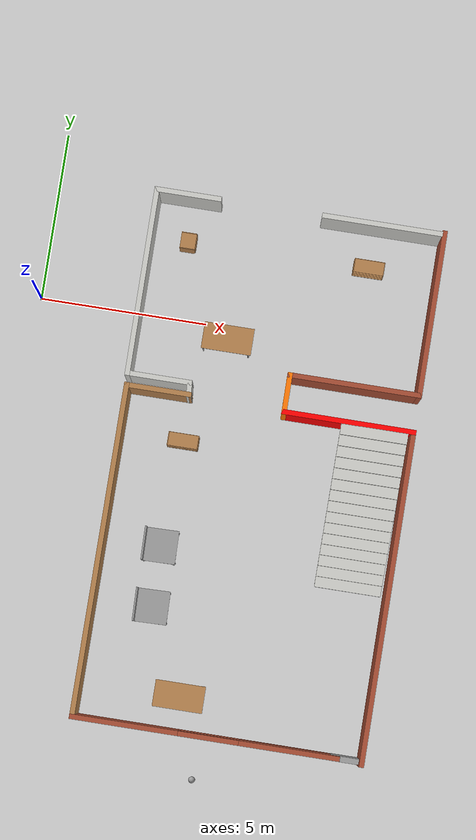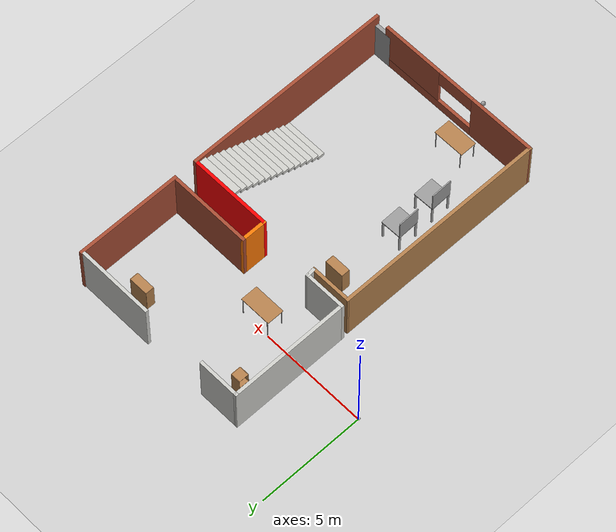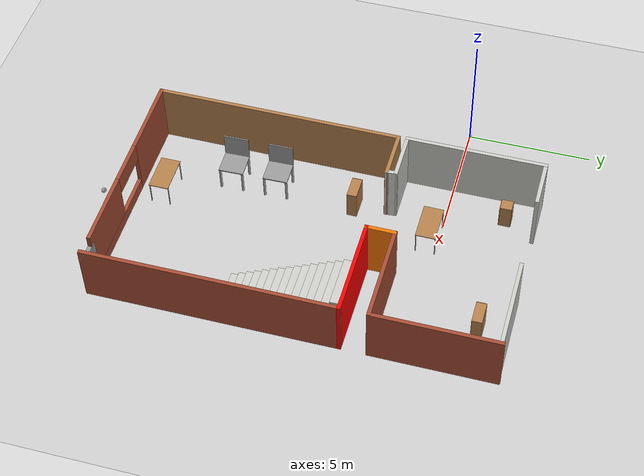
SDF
<sdf version="1.6">
 <world name="default">
  <plugin name="helloworld" filename="libhelloworld.so"/>
  <light name="sun" type="directional">
   <pose>0 0 10 0 -0 0</pose>
   <diffuse>0.8 0.8 0.8 1</diffuse>
   <specular>0.2 0.2 0.2 1</specular>
   <attenuation>
    <range>1000</range>
    <constant>0.9</constant>
    <linear>0.01</linear>
    <quadratic>0.001</quadratic>
   </attenuation>
   <direction>-0.5 0.1 -0.9</direction>
  </light>
  <model name="ground_plane">
   <static>1</static>
   <link name="link">
    <collision name="collision">
     <geometry><plane><normal>0 0 1</normal><size>100 100</size></plane></geometry>
     <surface>
      <contact><collide_bitmask>65535</collide_bitmask></contact>
      <friction><ode><mu>100</mu><mu2>50</mu2></ode></friction>
     </surface>
    </collision>
    <visual name="visual">
     <cast_shadows>0</cast_shadows>
     <geometry><plane><normal>0 0 1</normal><size>100 100</size></plane></geometry>
     <material>
      <script><uri>file://media/materials/scripts/gazebo.material</uri><name>Gazebo/Grey</name></script>
     </material>
    </visual>
   </link>
  </model>
  <gravity>0 0 -9.8</gravity>
  <magnetic_field>6e-06 2.3e-05 -4.2e-05</magnetic_field>
  <atmosphere type="adiabatic"/>
  <physics name="default_physics" default="0" type="ode">
   <max_step_size>0.001</max_step_size>
   <real_time_factor>1</real_time_factor>
   <real_time_update_rate>1000</real_time_update_rate>
  </physics>
  <scene><ambient>0.4 0.4 0.4 1</ambient><background>0.7 0.7 0.7 1</background><shadows>1</shadows></scene>
  <spherical_coordinates>
   <surface_model>EARTH_WGS84</surface_model>
   <latitude_deg>0</latitude_deg>
   <longitude_deg>0</longitude_deg>
   <elevation>0</elevation>
   <heading_deg>0</heading_deg>
  </spherical_coordinates>
  <model name="House_level1">
   <pose>7.29089 -4.3582 0 0 -0 0</pose>
   <link name="Door_0">
    <collision name="Door_0_Collision">
     <geometry><box><size>0.9 0.17 2</size></box></geometry>
     <pose>0 0 1 0 -0 0</pose>
    </collision>
    <visual name="Door_0_Visual">
     <pose>0 0 1 0 -0 0</pose>
     <geometry><box><size>0.9 0.17 2</size></box></geometry>
     <material>
      <script><uri>file://media/materials/scripts/gazebo.material</uri><name>Gazebo/Grey</name></script>
     </material>
    </visual>
    <pose>3.83051 -7.8386 0 0 -0 0</pose>
   </link>
   <link name="Stairs_1">
    <visual name="Stairs_1_Visual_0">
     <pose>3.1486 -2.76175 0.083333 0 -0 -3.14159</pose>
     <geometry><box><size>2 0.320133 0.166667</size></box></geometry>
     <material>
      <script><uri>file://media/materials/scripts/gazebo.material</uri><name>Gazebo/CeilingTiled</name></script>
      <ambient>0.760784 0.662745 0.627451 1</ambient>
     </material>
     <meta><layer>0</layer></meta>
    </visual>
    <collision name="Stairs_1_Collision_0">
     <geometry><box><size>2 0.320133 0.166667</size></box></geometry>
     <pose>3.1486 -2.76175 0.083333 0 -0 -3.14159</pose>
    </collision>
    <visual name="Stairs_1_Visual_1">
     <pose>3.1486 -2.44161 0.25 0 -0 -3.14159</pose>
     <geometry><box><size>2 0.320133 0.166667</size></box></geometry>
     <material>
      <script><uri>file://media/materials/scripts/gazebo.material</uri><name>Gazebo/CeilingTiled</name></script>
      <ambient>0.760784 0.662745 0.627451 1</ambient>
     </material>
     <meta><layer>0</layer></meta>
    </visual>
    <collision name="Stairs_1_Collision_1">
     <geometry><box><size>2 0.320133 0.166667</size></box></geometry>
     <pose>3.1486 -2.44161 0.25 0 -0 -3.14159</pose>
    </collision>
    <visual name="Stairs_1_Visual_2">
     <pose>3.1486 -2.12148 0.416667 0 -0 -3.14159</pose>
     <geometry><box><size>2 0.320133 0.166667</size></box></geometry>
     <material>
      <script><uri>file://media/materials/scripts/gazebo.material</uri><name>Gazebo/CeilingTiled</name></script>
      <ambient>0.760784 0.662745 0.627451 1</ambient>
     </material>
     <meta><layer>0</layer></meta>
    </visual>
    <collision name="Stairs_1_Collision_2">
     <geometry><box><size>2 0.320133 0.166667</size></box></geometry>
     <pose>3.1486 -2.12148 0.416667 0 -0 -3.14159</pose>
    </collision>
    <visual name="Stairs_1_Visual_3">
     <pose>3.1486 -1.80135 0.583333 0 -0 -3.14159</pose>
     <geometry><box><size>2 0.320133 0.166667</size></box></geometry>
     <material>
      <script><uri>file://media/materials/scripts/gazebo.material</uri><name>Gazebo/CeilingTiled</name></script>
      <ambient>0.760784 0.662745 0.627451 1</ambient>
     </material>
     <meta><layer>0</layer></meta>
    </visual>
    <collision name="Stairs_1_Collision_3">
     <geometry><box><size>2 0.320133 0.166667</size></box></geometry>
     <pose>3.1486 -1.80135 0.583333 0 -0 -3.14159</pose>
    </collision>
    <visual name="Stairs_1_Visual_4">
     <pose>3.1486 -1.48121 0.75 0 -0 -3.14159</pose>
     <geometry><box><size>2 0.320133 0.166667</size></box></geometry>
     <material>
      <script><uri>file://media/materials/scripts/gazebo.material</uri><name>Gazebo/CeilingTiled</name></script>
      <ambient>0.760784 0.662745 0.627451 1</ambient>
     </material>
     <meta><layer>0</layer></meta>
    </visual>
    <collision name="Stairs_1_Collision_4">
     <geometry><box><size>2 0.320133 0.166667</size></box></geometry>
     <pose>3.1486 -1.48121 0.75 0 -0 -3.14159</pose>
    </collision>
    <visual name="Stairs_1_Visual_5">
     <pose>3.1486 -1.16108 0.916667 0 -0 -3.14159</pose>
     <geometry><box><size>2 0.320133 0.166667</size></box></geometry>
     <material>
      <script><uri>file://media/materials/scripts/gazebo.material</uri><name>Gazebo/CeilingTiled</name></script>
      <ambient>0.760784 0.662745 0.627451 1</ambient>
     </material>
     <meta><layer>0</layer></meta>
    </visual>
    <collision name="Stairs_1_Collision_5">
     <geometry><box><size>2 0.320133 0.166667</size></box></geometry>
     <pose>3.1486 -1.16108 0.916667 0 -0 -3.14159</pose>
    </collision>
    <visual name="Stairs_1_Visual_6">
     <pose>3.1486 -0.840946 1.08333 0 -0 -3.14159</pose>
     <geometry><box><size>2 0.320133 0.166667</size></box></geometry>
     <material>
      <script><uri>file://media/materials/scripts/gazebo.material</uri><name>Gazebo/CeilingTiled</name></script>
      <ambient>0.760784 0.662745 0.627451 1</ambient>
     </material>
     <meta><layer>0</layer></meta>
    </visual>
    <collision name="Stairs_1_Collision_6">
     <geometry><box><size>2 0.320133 0.166667</size></box></geometry>
     <pose>3.1486 -0.840946 1.08333 0 -0 -3.14159</pose>
    </collision>
    <visual name="Stairs_1_Visual_7">
     <pose>3.1486 -0.520813 1.25 0 -0 -3.14159</pose>
     <geometry><box><size>2 0.320133 0.166667</size></box></geometry>
     <material>
      <script><uri>file://media/materials/scripts/gazebo.material</uri><name>Gazebo/CeilingTiled</name></script>
      <ambient>0.760784 0.662745 0.627451 1</ambient>
     </material>
     <meta><layer>0</layer></meta>
    </visual>
    <collision name="Stairs_1_Collision_7">
     <geometry><box><size>2 0.320133 0.166667</size></box></geometry>
     <pose>3.1486 -0.520813 1.25 0 -0 -3.14159</pose>
    </collision>
    <visual name="Stairs_1_Visual_8">
     <pose>3.1486 -0.200679 1.41667 0 -0 -3.14159</pose>
     <geometry><box><size>2 0.320133 0.166667</size></box></geometry>
     <material>
      <script><uri>file://media/materials/scripts/gazebo.material</uri><name>Gazebo/CeilingTiled</name></script>
      <ambient>0.760784 0.662745 0.627451 1</ambient>
     </material>
     <meta><layer>0</layer></meta>
    </visual>
    <collision name="Stairs_1_Collision_8">
     <geometry><box><size>2 0.320133 0.166667</size></box></geometry>
     <pose>3.1486 -0.200679 1.41667 0 -0 -3.14159</pose>
    </collision>
    <visual name="Stairs_1_Visual_9">
     <pose>3.1486 0.119454 1.58333 0 -0 -3.14159</pose>
     <geometry><box><size>2 0.320133 0.166667</size></box></geometry>
     <material>
      <script><uri>file://media/materials/scripts/gazebo.material</uri><name>Gazebo/CeilingTiled</name></script>
      <ambient>0.760784 0.662745 0.627451 1</ambient>
     </material>
     <meta><layer>0</layer></meta>
    </visual>
    <collision name="Stairs_1_Collision_9">
     <geometry><box><size>2 0.320133 0.166667</size></box></geometry>
     <pose>3.1486 0.119454 1.58333 0 -0 -3.14159</pose>
    </collision>
    <visual name="Stairs_1_Visual_10">
     <pose>3.1486 0.439587 1.75 0 -0 -3.14159</pose>
     <geometry><box><size>2 0.320133 0.166667</size></box></geometry>
     <material>
      <script><uri>file://media/materials/scripts/gazebo.material</uri><name>Gazebo/CeilingTiled</name></script>
      <ambient>0.760784 0.662745 0.627451 1</ambient>
     </material>
     <meta><layer>0</layer></meta>
    </visual>
    <collision name="Stairs_1_Collision_10">
     <geometry><box><size>2 0.320133 0.166667</size></box></geometry>
     <pose>3.1486 0.439587 1.75 0 -0 -3.14159</pose>
    </collision>
    <visual name="Stairs_1_Visual_11">
     <pose>3.1486 0.759721 1.91667 0 -0 -3.14159</pose>
     <geometry><box><size>2 0.320133 0.166667</size></box></geometry>
     <material>
      <script><uri>file://media/materials/scripts/gazebo.material</uri><name>Gazebo/CeilingTiled</name></script>
      <ambient>0.760784 0.662745 0.627451 1</ambient>
     </material>
     <meta><layer>0</layer></meta>
    </visual>
    <collision name="Stairs_1_Collision_11">
     <geometry><box><size>2 0.320133 0.166667</size></box></geometry>
     <pose>3.1486 0.759721 1.91667 0 -0 -3.14159</pose>
    </collision>
    <visual name="Stairs_1_Visual_12">
     <pose>3.1486 1.07985 2.08333 0 -0 -3.14159</pose>
     <geometry><box><size>2 0.320133 0.166667</size></box></geometry>
     <material>
      <script><uri>file://media/materials/scripts/gazebo.material</uri><name>Gazebo/CeilingTiled</name></script>
      <ambient>0.760784 0.662745 0.627451 1</ambient>
     </material>
     <meta><layer>0</layer></meta>
    </visual>
    <collision name="Stairs_1_Collision_12">
     <geometry><box><size>2 0.320133 0.166667</size></box></geometry>
     <pose>3.1486 1.07985 2.08333 0 -0 -3.14159</pose>
    </collision>
    <visual name="Stairs_1_Visual_13">
     <pose>3.1486 1.39999 2.25 0 -0 -3.14159</pose>
     <geometry><box><size>2 0.320133 0.166667</size></box></geometry>
     <material>
      <script><uri>file://media/materials/scripts/gazebo.material</uri><name>Gazebo/CeilingTiled</name></script>
      <ambient>0.760784 0.662745 0.627451 1</ambient>
     </material>
     <meta><layer>0</layer></meta>
    </visual>
    <collision name="Stairs_1_Collision_13">
     <geometry><box><size>2 0.320133 0.166667</size></box></geometry>
     <pose>3.1486 1.39999 2.25 0 -0 -3.14159</pose>
    </collision>
    <visual name="Stairs_1_Visual_14">
     <pose>3.1486 1.72012 2.41667 0 -0 -3.14159</pose>
     <geometry><box><size>2 0.320133 0.166667</size></box></geometry>
     <material>
      <script><uri>file://media/materials/scripts/gazebo.material</uri><name>Gazebo/CeilingTiled</name></script>
      <ambient>0.760784 0.662745 0.627451 1</ambient>
     </material>
     <meta><layer>0</layer></meta>
    </visual>
    <collision name="Stairs_1_Collision_14">
     <geometry><box><size>2 0.320133 0.166667</size></box></geometry>
     <pose>3.1486 1.72012 2.41667 0 -0 -3.14159</pose>
    </collision>
   </link>
   <link name="Wall_0">
    <pose>-0.364367 -7.835 0 0 -0 0</pose>
    <visual name="Wall_0_Visual_0">
     <pose>-2.39909 0 1.25 0 -0 0</pose>
     <geometry><box><size>3.20181 0.15 2.5</size></box></geometry>
     <material>
      <script><uri>file://media/materials/scripts/gazebo.material</uri><name>Gazebo/Bricks</name></script>
      <ambient>1 0 0 1</ambient>
     </material>
     <meta><layer>0</layer></meta>
    </visual>
    <collision name="Wall_0_Collision_0">
     <geometry><box><size>3.20181 0.15 2.5</size></box></geometry>
     <pose>-2.39909 0 1.25 0 -0 0</pose>
    </collision>
    <visual name="Wall_0_Visual_1">
     <pose>1.60091 0 0.25 0 -0 0</pose>
     <geometry><box><size>4.79819 0.15 0.5</size></box></geometry>
     <material>
      <script><uri>file://media/materials/scripts/gazebo.material</uri><name>Gazebo/Bricks</name></script>
      <ambient>1 0 0 1</ambient>
     </material>
     <meta><layer>0</layer></meta>
    </visual>
    <collision name="Wall_0_Collision_1">
     <geometry><box><size>4.79819 0.15 0.5</size></box></geometry>
     <pose>1.60091 0 0.25 0 -0 0</pose>
    </collision>
    <visual name="Wall_0_Visual_2">
     <pose>2.5009 0 1.5 0 -0 0</pose>
     <geometry><box><size>2.99819 0.15 2</size></box></geometry>
     <material>
      <script><uri>file://media/materials/scripts/gazebo.material</uri><name>Gazebo/Bricks</name></script>
      <ambient>1 0 0 1</ambient>
     </material>
     <meta><layer>0</layer></meta>
    </visual>
    <collision name="Wall_0_Collision_2">
     <geometry><box><size>2.99819 0.15 2</size></box></geometry>
     <pose>2.5009 0 1.5 0 -0 0</pose>
    </collision>
    <visual name="Wall_0_Visual_3">
     <pose>0.101809 0 2.1 0 -0 0</pose>
     <geometry><box><size>1.8 0.15 0.8</size></box></geometry>
     <material>
      <script><uri>file://media/materials/scripts/gazebo.material</uri><name>Gazebo/Bricks</name></script>
      <ambient>1 0 0 1</ambient>
     </material>
     <meta><layer>0</layer></meta>
    </visual>
    <collision name="Wall_0_Collision_3">
     <geometry><box><size>1.8 0.15 0.8</size></box></geometry>
     <pose>0.101809 0 2.1 0 -0 0</pose>
    </collision>
   </link>
   <link name="Wall_11">
    <collision name="Wall_11_Collision">
     <geometry><box><size>1.25 0.15 2.5</size></box></geometry>
     <pose>0 0 1.25 0 -0 0</pose>
    </collision>
    <visual name="Wall_11_Visual">
     <pose>0 0 1.25 0 -0 0</pose>
     <geometry><box><size>1.25 0.15 2.5</size></box></geometry>
     <material>
      <script><uri>file://media/materials/scripts/gazebo.material</uri><name>Gazebo/Grey</name></script>
      <ambient>0.996078 0.47451 0.0196078 1</ambient>
     </material>
     <meta><layer>0</layer></meta>
    </visual>
    <pose>0.439633 2.5 0 0 -0 1.5708</pose>
   </link>
   <link name="Wall_12">
    <collision name="Wall_12_Collision">
     <geometry><box><size>4 0.15 2.5</size></box></geometry>
     <pose>0 0 1.25 0 -0 0</pose>
    </collision>
    <visual name="Wall_12_Visual">
     <pose>0 0 1.25 0 -0 0</pose>
     <geometry><box><size>4 0.15 2.5</size></box></geometry>
     <material>
      <script><uri>file://media/materials/scripts/gazebo.material</uri><name>Gazebo/Bricks</name></script>
      <ambient>1 0 0 1</ambient>
     </material>
     <meta><layer>0</layer></meta>
    </visual>
    <pose>2.36463 3.05 0 0 -0 0</pose>
   </link>
   <link name="Wall_13">
    <collision name="Wall_13_Collision">
     <geometry><box><size>5 0.15 2.5</size></box></geometry>
     <pose>0 0 1.25 0 -0 0</pose>
    </collision>
    <visual name="Wall_13_Visual">
     <pose>0 0 1.25 0 -0 0</pose>
     <geometry><box><size>5 0.15 2.5</size></box></geometry>
     <material>
      <script><uri>file://media/materials/scripts/gazebo.material</uri><name>Gazebo/Bricks</name></script>
      <ambient>1 0 0 1</ambient>
     </material>
     <meta><layer>0</layer></meta>
    </visual>
    <pose>4.28963 5.475 0 0 -0 1.5708</pose>
   </link>
   <link name="Wall_16">
    <collision name="Wall_16_Collision">
     <geometry><box><size>0.501746 0.15 2.5</size></box></geometry>
     <pose>0 0 1.25 0 -0 0</pose>
    </collision>
    <visual name="Wall_16_Visual">
     <pose>0 0 1.25 0 -0 0</pose>
     <geometry><box><size>0.501746 0.15 2.5</size></box></geometry>
     <material>
      <script><uri>file://media/materials/scripts/gazebo.material</uri><name>Gazebo/CeilingTiled</name></script>
      <ambient>0.996078 0.47451 0.0196078 1</ambient>
     </material>
     <meta><layer>0</layer></meta>
    </visual>
    <pose>-2.42187 2.19 0 0 -0 1.67047</pose>
   </link>
   <link name="Wall_17">
    <collision name="Wall_17_Collision">
     <geometry><box><size>2 0.15 2.5</size></box></geometry>
     <pose>0 0 1.25 0 -0 0</pose>
    </collision>
    <visual name="Wall_17_Visual">
     <pose>0 0 1.25 0 -0 0</pose>
     <geometry><box><size>2 0.15 2.5</size></box></geometry>
     <material>
      <script><uri>file://media/materials/scripts/gazebo.material</uri><name>Gazebo/CeilingTiled</name></script>
      <ambient>0.760784 0.662745 0.627451 1</ambient>
     </material>
     <meta><layer>0</layer></meta>
    </visual>
    <pose>-3.36437 2.365 0 0 -0 3.14159</pose>
   </link>
   <link name="Wall_18">
    <collision name="Wall_18_Collision">
     <geometry><box><size>5.646 0.15 2.5</size></box></geometry>
     <pose>0 0 1.25 0 -0 0</pose>
    </collision>
    <visual name="Wall_18_Visual">
     <pose>0 0 1.25 0 -0 0</pose>
     <geometry><box><size>5.646 0.15 2.5</size></box></geometry>
     <material>
      <script><uri>file://media/materials/scripts/gazebo.material</uri><name>Gazebo/CeilingTiled</name></script>
      <ambient>1 1 1 1</ambient>
     </material>
     <meta><layer>0</layer></meta>
    </visual>
    <pose>-4.28937 5.113 0 0 -0 1.5708</pose>
   </link>
   <link name="Wall_21">
    <pose>-0.064367 7.861 0 0 -0 0</pose>
    <visual name="Wall_21_Visual_0">
     <pose>-3.29914 0 1.25 0 -0 0</pose>
     <geometry><box><size>2.00172 0.15 2.5</size></box></geometry>
     <material>
      <script><uri>file://media/materials/scripts/gazebo.material</uri><name>Gazebo/CeilingTiled</name></script>
      <ambient>1 1 1 1</ambient>
     </material>
     <meta><layer>0</layer></meta>
    </visual>
    <collision name="Wall_21_Collision_0">
     <geometry><box><size>2.00172 0.15 2.5</size></box></geometry>
     <pose>-3.29914 0 1.25 0 -0 0</pose>
    </collision>
    <visual name="Wall_21_Visual_1">
     <pose>2.50086 0 1.25 0 -0 0</pose>
     <geometry><box><size>3.59828 0.15 2.5</size></box></geometry>
     <material>
      <script><uri>file://media/materials/scripts/gazebo.material</uri><name>Gazebo/CeilingTiled</name></script>
      <ambient>1 1 1 1</ambient>
     </material>
     <meta><layer>0</layer></meta>
    </visual>
    <collision name="Wall_21_Collision_1">
     <geometry><box><size>3.59828 0.15 2.5</size></box></geometry>
     <pose>2.50086 0 1.25 0 -0 0</pose>
    </collision>
   </link>
   <link name="Wall_3">
    <collision name="Wall_3_Collision">
     <geometry><box><size>10 0.15 2.5</size></box></geometry>
     <pose>0 0 1.25 0 -0 0</pose>
    </collision>
    <visual name="Wall_3_Visual">
     <pose>0 0 1.25 0 -0 0</pose>
     <geometry><box><size>10 0.15 2.5</size></box></geometry>
     <material>
      <script><uri>file://media/materials/scripts/gazebo.material</uri><name>Gazebo/Bricks</name></script>
      <ambient>1 0 0 1</ambient>
     </material>
     <meta><layer>0</layer></meta>
    </visual>
    <pose>4.28963 -2.975 0 0 -0 1.5708</pose>
   </link>
   <link name="Wall_5">
    <collision name="Wall_5_Collision">
     <geometry><box><size>10 0.15 2.5</size></box></geometry>
     <pose>0 0 1.25 0 -0 0</pose>
    </collision>
    <visual name="Wall_5_Visual">
     <pose>0 0 1.25 0 -0 0</pose>
     <geometry><box><size>10 0.15 2.5</size></box></geometry>
     <material>
      <script><uri>file://media/materials/scripts/gazebo.material</uri><name>Gazebo/Wood</name></script>
      <ambient>0.760784 0.662745 0.627451 1</ambient>
     </material>
     <meta><layer>0</layer></meta>
    </visual>
    <pose>-4.27187 -2.91 0 0 -0 1.56724</pose>
   </link>
   <link name="Wall_7">
    <collision name="Wall_7_Collision">
     <geometry><box><size>4 0.15 2.5</size></box></geometry>
     <pose>0 0 1.25 0 -0 0</pose>
    </collision>
    <visual name="Wall_7_Visual">
     <pose>0 0 1.25 0 -0 0</pose>
     <geometry><box><size>4 0.15 2.5</size></box></geometry>
     <material>
      <script><uri>file://media/materials/scripts/gazebo.material</uri><name>Gazebo/Grey</name></script>
      <ambient>1 0 0 1</ambient>
     </material>
     <meta><layer>0</layer></meta>
    </visual>
    <pose>2.36463 1.95 0 0 -0 3.14159</pose>
   </link>
   <link name="Wall_9">
    <collision name="Wall_9_Collision">
     <geometry><box><size>2 0.15 2.5</size></box></geometry>
     <pose>0 0 1.25 0 -0 0</pose>
    </collision>
    <visual name="Wall_9_Visual">
     <pose>0 0 1.25 0 -0 0</pose>
     <geometry><box><size>2 0.15 2.5</size></box></geometry>
     <material>
      <script><uri>file://media/materials/scripts/gazebo.material</uri><name>Gazebo/Wood</name></script>
      <ambient>0.760784 0.662745 0.627451 1</ambient>
     </material>
     <meta><layer>0</layer></meta>
    </visual>
    <pose>-3.32937 2.015 0 0 -0 0</pose>
   </link>
   <static>1</static>
  </model>
  <model name="cabinet">
   <static>1</static>
   <link name="cabinet_bottom_plate">
    <inertial>
     <pose>0 0 -1 0 -0 0</pose>
     <inertia><ixx>2.05</ixx><ixy>0</ixy><ixz>0</ixz><iyy>2.05</iyy><iyz>0</iyz><izz>2.05</izz></inertia>
     <mass>25</mass>
    </inertial>
    <collision name="cabinet_bottom_plate_geom">
     <pose>0 0 0.01 0 -0 0</pose>
     <geometry><box><size>0.45 0.45 0.02</size></box></geometry>
    </collision>
    <visual name="cabinet_bottom_plate_geom_visual">
     <pose>0 0 0.01 0 -0 0</pose>
     <geometry><box><size>0.45 0.45 0.02</size></box></geometry>
     <material>
      <script><uri>file://media/materials/scripts/gazebo.material</uri><name>Gazebo/Wood</name></script>
     </material>
    </visual>
    <collision name="cabinet_bottom_plate_geom_cabinet_back_plate">
     <pose>0.235 0 0.51 0 -0 0</pose>
     <geometry><box><size>0.02 0.45 1.02</size></box></geometry>
    </collision>
    <visual name="cabinet_bottom_plate_geom_cabinet_back_plate_visual">
     <pose>0.235 0 0.51 0 -0 0</pose>
     <geometry><box><size>0.02 0.45 1.02</size></box></geometry>
     <material>
      <script><uri>file://media/materials/scripts/gazebo.material</uri><name>Gazebo/Wood</name></script>
     </material>
    </visual>
    <collision name="cabinet_bottom_plate_geom_cabinet_left_plate">
     <pose>0 0.235 0.51 0 -0 0</pose>
     <geometry><box><size>0.45 0.02 1.02</size></box></geometry>
    </collision>
    <visual name="cabinet_bottom_plate_geom_cabinet_left_plate_visual">
     <pose>0 0.235 0.51 0 -0 0</pose>
     <geometry><box><size>0.45 0.02 1.02</size></box></geometry>
     <material>
      <script><uri>file://media/materials/scripts/gazebo.material</uri><name>Gazebo/Wood</name></script>
     </material>
    </visual>
    <collision name="cabinet_bottom_plate_geom_cabinet_middle_plate">
     <pose>0 0 0.51 0 -0 0</pose>
     <geometry><box><size>0.45 0.45 0.02</size></box></geometry>
    </collision>
    <visual name="cabinet_bottom_plate_geom_cabinet_middle_plate_visual">
     <pose>0 0 0.51 0 -0 0</pose>
     <geometry><box><size>0.45 0.45 0.02</size></box></geometry>
     <material>
      <script><uri>file://media/materials/scripts/gazebo.material</uri><name>Gazebo/Wood</name></script>
     </material>
    </visual>
    <collision name="cabinet_bottom_plate_geom_cabinet_right_plate">
     <pose>0 -0.235 0.51 0 -0 0</pose>
     <geometry><box><size>0.45 0.02 1.02</size></box></geometry>
    </collision>
    <visual name="cabinet_bottom_plate_geom_cabinet_right_plate_visual">
     <pose>0 -0.235 0.51 0 -0 0</pose>
     <geometry><box><size>0.45 0.02 1.02</size></box></geometry>
     <material>
      <script><uri>file://media/materials/scripts/gazebo.material</uri><name>Gazebo/Wood</name></script>
     </material>
    </visual>
    <collision name="cabinet_bottom_plate_geom_cabinet_top_plate">
     <pose>0 0 1.01 0 -0 0</pose>
     <geometry><box><size>0.45 0.45 0.02</size></box></geometry>
    </collision>
    <visual name="cabinet_bottom_plate_geom_cabinet_top_plate_visual">
     <pose>0 0 1.01 0 -0 0</pose>
     <geometry><box><size>0.45 0.45 0.02</size></box></geometry>
     <material>
      <script><uri>file://media/materials/scripts/gazebo.material</uri><name>Gazebo/Wood</name></script>
     </material>
    </visual>
   </link>
   <pose>4.10378 2.30036 0.012182 0 -0 0</pose>
  </model>
  <model name="bookshelf">
   <static>1</static>
   <link name="link">
    <inertial><mass>1</mass></inertial>
    <collision name="back">
     <pose>0 0.005 0.6 0 -0 0</pose>
     <geometry><box><size>0.9 0.01 1.2</size></box></geometry>
    </collision>
    <visual name="visual1">
     <pose>0 0.005 0.6 0 -0 0</pose>
     <geometry><box><size>0.9 0.01 1.2</size></box></geometry>
     <material>
      <script><uri>file://media/materials/scripts/gazebo.material</uri><name>Gazebo/Wood</name></script>
     </material>
    </visual>
    <collision name="left_side">
     <pose>0.45 -0.195 0.6 0 -0 0</pose>
     <geometry><box><size>0.02 0.4 1.2</size></box></geometry>
    </collision>
    <visual name="visual2">
     <pose>0.45 -0.195 0.6 0 -0 0</pose>
     <geometry><box><size>0.02 0.4 1.2</size></box></geometry>
     <material>
      <script><uri>file://media/materials/scripts/gazebo.material</uri><name>Gazebo/Wood</name></script>
     </material>
    </visual>
    <collision name="right_side">
     <pose>-0.45 -0.195 0.6 0 -0 0</pose>
     <geometry><box><size>0.02 0.4 1.2</size></box></geometry>
    </collision>
    <visual name="visual3">
     <pose>-0.45 -0.195 0.6 0 -0 0</pose>
     <geometry><box><size>0.02 0.4 1.2</size></box></geometry>
     <material>
      <script><uri>file://media/materials/scripts/gazebo.material</uri><name>Gazebo/Wood</name></script>
     </material>
    </visual>
    <collision name="bottom">
     <pose>0 -0.195 0.03 0 -0 0</pose>
     <geometry><box><size>0.88 0.4 0.06</size></box></geometry>
    </collision>
    <visual name="visual4">
     <pose>0 -0.195 0.03 0 -0 0</pose>
     <geometry><box><size>0.88 0.4 0.06</size></box></geometry>
     <material>
      <script><uri>file://media/materials/scripts/gazebo.material</uri><name>Gazebo/Wood</name></script>
     </material>
    </visual>
    <collision name="top">
     <pose>0 -0.195 1.19 0 -0 0</pose>
     <geometry><box><size>0.88 0.4 0.02</size></box></geometry>
    </collision>
    <visual name="visual5">
     <pose>0 -0.195 1.19 0 -0 0</pose>
     <geometry><box><size>0.88 0.4 0.02</size></box></geometry>
     <material>
      <script><uri>file://media/materials/scripts/gazebo.material</uri><name>Gazebo/Wood</name></script>
     </material>
    </visual>
    <collision name="low_shelf">
     <pose>0 -0.195 0.43 0 -0 0</pose>
     <geometry><box><size>0.88 0.4 0.02</size></box></geometry>
    </collision>
    <visual name="visual6">
     <pose>0 -0.195 0.43 0 -0 0</pose>
     <geometry><box><size>0.88 0.4 0.02</size></box></geometry>
     <material>
      <script><uri>file://media/materials/scripts/gazebo.material</uri><name>Gazebo/Wood</name></script>
     </material>
    </visual>
    <collision name="high_shelf">
     <pose>0 -0.195 0.8 0 -0 0</pose>
     <geometry><box><size>0.88 0.4 0.02</size></box></geometry>
    </collision>
    <visual name="visual7">
     <pose>0 -0.195 0.8 0 -0 0</pose>
     <geometry><box><size>0.88 0.4 0.02</size></box></geometry>
     <material>
      <script><uri>file://media/materials/scripts/gazebo.material</uri><name>Gazebo/Wood</name></script>
     </material>
    </visual>
   </link>
   <pose>9.55634 2.54345 0 0 -0 0</pose>
  </model>
  <model name="bookshelf_0">
   <static>1</static>
   <link name="link">
    <inertial><mass>1</mass></inertial>
    <collision name="back">
     <pose>0 0.005 0.6 0 -0 0</pose>
     <geometry><box><size>0.9 0.01 1.2</size></box></geometry>
    </collision>
    <visual name="visual1">
     <pose>0 0.005 0.6 0 -0 0</pose>
     <geometry><box><size>0.9 0.01 1.2</size></box></geometry>
     <material>
      <script><uri>file://media/materials/scripts/gazebo.material</uri><name>Gazebo/Wood</name></script>
     </material>
    </visual>
    <collision name="left_side">
     <pose>0.45 -0.195 0.6 0 -0 0</pose>
     <geometry><box><size>0.02 0.4 1.2</size></box></geometry>
    </collision>
    <visual name="visual2">
     <pose>0.45 -0.195 0.6 0 -0 0</pose>
     <geometry><box><size>0.02 0.4 1.2</size></box></geometry>
     <material>
      <script><uri>file://media/materials/scripts/gazebo.material</uri><name>Gazebo/Wood</name></script>
     </material>
    </visual>
    <collision name="right_side">
     <pose>-0.45 -0.195 0.6 0 -0 0</pose>
     <geometry><box><size>0.02 0.4 1.2</size></box></geometry>
    </collision>
    <visual name="visual3">
     <pose>-0.45 -0.195 0.6 0 -0 0</pose>
     <geometry><box><size>0.02 0.4 1.2</size></box></geometry>
     <material>
      <script><uri>file://media/materials/scripts/gazebo.material</uri><name>Gazebo/Wood</name></script>
     </material>
    </visual>
    <collision name="bottom">
     <pose>0 -0.195 0.03 0 -0 0</pose>
     <geometry><box><size>0.88 0.4 0.06</size></box></geometry>
    </collision>
    <visual name="visual4">
     <pose>0 -0.195 0.03 0 -0 0</pose>
     <geometry><box><size>0.88 0.4 0.06</size></box></geometry>
     <material>
      <script><uri>file://media/materials/scripts/gazebo.material</uri><name>Gazebo/Wood</name></script>
     </material>
    </visual>
    <collision name="top">
     <pose>0 -0.195 1.19 0 -0 0</pose>
     <geometry><box><size>0.88 0.4 0.02</size></box></geometry>
    </collision>
    <visual name="visual5">
     <pose>0 -0.195 1.19 0 -0 0</pose>
     <geometry><box><size>0.88 0.4 0.02</size></box></geometry>
     <material>
      <script><uri>file://media/materials/scripts/gazebo.material</uri><name>Gazebo/Wood</name></script>
     </material>
    </visual>
    <collision name="low_shelf">
     <pose>0 -0.195 0.43 0 -0 0</pose>
     <geometry><box><size>0.88 0.4 0.02</size></box></geometry>
    </collision>
    <visual name="visual6">
     <pose>0 -0.195 0.43 0 -0 0</pose>
     <geometry><box><size>0.88 0.4 0.02</size></box></geometry>
     <material>
      <script><uri>file://media/materials/scripts/gazebo.material</uri><name>Gazebo/Wood</name></script>
     </material>
    </visual>
    <collision name="high_shelf">
     <pose>0 -0.195 0.8 0 -0 0</pose>
     <geometry><box><size>0.88 0.4 0.02</size></box></geometry>
    </collision>
    <visual name="visual7">
     <pose>0 -0.195 0.8 0 -0 0</pose>
     <geometry><box><size>0.88 0.4 0.02</size></box></geometry>
     <material>
      <script><uri>file://media/materials/scripts/gazebo.material</uri><name>Gazebo/Wood</name></script>
     </material>
    </visual>
   </link>
   <pose>4.90189 -3.43425 0 0 -0 0</pose>
  </model>
  <model name="table">
   <static>1</static>
   <link name="link">
    <collision name="surface">
     <pose>0 0 1 0 -0 0</pose>
     <geometry><box><size>1.5 0.8 0.03</size></box></geometry>
     <surface><friction><ode><mu>0.6</mu><mu2>0.6</mu2></ode></friction></surface>
    </collision>
    <visual name="visual1">
     <pose>0 0 1 0 -0 0</pose>
     <geometry><box><size>1.5 0.8 0.03</size></box></geometry>
     <material>
      <script><uri>file://media/materials/scripts/gazebo.material</uri><name>Gazebo/Wood</name></script>
     </material>
    </visual>
    <collision name="front_left_leg">
     <pose>0.68 0.38 0.5 0 -0 0</pose>
     <geometry><cylinder><radius>0.02</radius><length>1</length></cylinder></geometry>
    </collision>
    <visual name="front_left_leg">
     <pose>0.68 0.38 0.5 0 -0 0</pose>
     <geometry><cylinder><radius>0.02</radius><length>1</length></cylinder></geometry>
     <material>
      <script><uri>file://media/materials/scripts/gazebo.material</uri><name>Gazebo/Grey</name></script>
     </material>
    </visual>
    <collision name="front_right_leg">
     <pose>0.68 -0.38 0.5 0 -0 0</pose>
     <geometry><cylinder><radius>0.02</radius><length>1</length></cylinder></geometry>
    </collision>
    <visual name="front_right_leg">
     <pose>0.68 -0.38 0.5 0 -0 0</pose>
     <geometry><cylinder><radius>0.02</radius><length>1</length></cylinder></geometry>
     <material>
      <script><uri>file://media/materials/scripts/gazebo.material</uri><name>Gazebo/Grey</name></script>
     </material>
    </visual>
    <collision name="back_right_leg">
     <pose>-0.68 -0.38 0.5 0 -0 0</pose>
     <geometry><cylinder><radius>0.02</radius><length>1</length></cylinder></geometry>
    </collision>
    <visual name="back_right_leg">
     <pose>-0.68 -0.38 0.5 0 -0 0</pose>
     <geometry><cylinder><radius>0.02</radius><length>1</length></cylinder></geometry>
     <material>
      <script><uri>file://media/materials/scripts/gazebo.material</uri><name>Gazebo/Grey</name></script>
     </material>
    </visual>
    <collision name="back_left_leg">
     <pose>-0.68 0.38 0.5 0 -0 0</pose>
     <geometry><cylinder><radius>0.02</radius><length>1</length></cylinder></geometry>
    </collision>
    <visual name="back_left_leg">
     <pose>-0.68 0.38 0.5 0 -0 0</pose>
     <geometry><cylinder><radius>0.02</radius><length>1</length></cylinder></geometry>
     <material>
      <script><uri>file://media/materials/scripts/gazebo.material</uri><name>Gazebo/Grey</name></script>
     </material>
    </visual>
   </link>
   <pose>5.73049 -0.405648 0 0 -0 0</pose>
  </model>
  <model name="camera">
   <pose>-8e-06 1.1e-05 0.05 0 -0 0.000341</pose>
   <link name="link">
    <inertial>
     <mass>0.1</mass>
     <inertia>
      <ixx>0.000166667</ixx>
      <iyy>0.000166667</iyy>
      <izz>0.000166667</izz>
      <ixy>0</ixy>
      <ixz>0</ixz>
      <iyz>0</iyz>
     </inertia>
    </inertial>
    <collision name="collision"><geometry><box><size>0.1 0.1 0.1</size></box></geometry></collision>
    <visual name="visual"><geometry><box><size>0.1 0.1 0.1</size></box></geometry></visual>
    <sensor name="camera" type="camera">
     <camera name="__default__">
      <horizontal_fov>1.047</horizontal_fov>
      <image><width>320</width><height>240</height></image>
      <clip><near>0.1</near><far>100</far></clip>
     </camera>
     <always_on>1</always_on>
     <update_rate>30</update_rate>
     <visualize>1</visualize>
    </sensor>
   </link>
  </model>
  <model name="table_0">
   <static>1</static>
   <link name="link">
    <collision name="surface">
     <pose>0 0 1 0 -0 0</pose>
     <geometry><box><size>1.5 0.8 0.03</size></box></geometry>
     <surface><friction><ode><mu>0.6</mu><mu2>0.6</mu2></ode></friction></surface>
    </collision>
    <visual name="visual1">
     <pose>0 0 1 0 -0 0</pose>
     <geometry><box><size>1.5 0.8 0.03</size></box></geometry>
     <material>
      <script><uri>file://media/materials/scripts/gazebo.material</uri><name>Gazebo/Wood</name></script>
     </material>
    </visual>
    <collision name="front_left_leg">
     <pose>0.68 0.38 0.5 0 -0 0</pose>
     <geometry><cylinder><radius>0.02</radius><length>1</length></cylinder></geometry>
    </collision>
    <visual name="front_left_leg">
     <pose>0.68 0.38 0.5 0 -0 0</pose>
     <geometry><cylinder><radius>0.02</radius><length>1</length></cylinder></geometry>
     <material>
      <script><uri>file://media/materials/scripts/gazebo.material</uri><name>Gazebo/Grey</name></script>
     </material>
    </visual>
    <collision name="front_right_leg">
     <pose>0.68 -0.38 0.5 0 -0 0</pose>
     <geometry><cylinder><radius>0.02</radius><length>1</length></cylinder></geometry>
    </collision>
    <visual name="front_right_leg">
     <pose>0.68 -0.38 0.5 0 -0 0</pose>
     <geometry><cylinder><radius>0.02</radius><length>1</length></cylinder></geometry>
     <material>
      <script><uri>file://media/materials/scripts/gazebo.material</uri><name>Gazebo/Grey</name></script>
     </material>
    </visual>
    <collision name="back_right_leg">
     <pose>-0.68 -0.38 0.5 0 -0 0</pose>
     <geometry><cylinder><radius>0.02</radius><length>1</length></cylinder></geometry>
    </collision>
    <visual name="back_right_leg">
     <pose>-0.68 -0.38 0.5 0 -0 0</pose>
     <geometry><cylinder><radius>0.02</radius><length>1</length></cylinder></geometry>
     <material>
      <script><uri>file://media/materials/scripts/gazebo.material</uri><name>Gazebo/Grey</name></script>
     </material>
    </visual>
    <collision name="back_left_leg">
     <pose>-0.68 0.38 0.5 0 -0 0</pose>
     <geometry><cylinder><radius>0.02</radius><length>1</length></cylinder></geometry>
    </collision>
    <visual name="back_left_leg">
     <pose>-0.68 0.38 0.5 0 -0 0</pose>
     <geometry><cylinder><radius>0.02</radius><length>1</length></cylinder></geometry>
     <material>
      <script><uri>file://media/materials/scripts/gazebo.material</uri><name>Gazebo/Grey</name></script>
     </material>
    </visual>
   </link>
   <pose>5.97613 -11.1432 0 0 -0 0</pose>
  </model>
  <model name="my_Chair">
   <link name="link_0">
    <pose>-0.45 -0.370833 -0.245833 0 -0 0</pose>
    <inertial>
     <mass>1</mass>
     <inertia><ixx>0.145833</ixx><ixy>0</ixy><ixz>0</ixz><iyy>0.145833</iyy><iyz>0</iyz><izz>0.125</izz></inertia>
    </inertial>
    <visual name="visual">
     <geometry><cylinder><radius>0.05</radius><length>1</length></cylinder></geometry>
     <material>
      <lighting>1</lighting>
      <script><uri>file://media/materials/scripts/gazebo.material</uri><name>Gazebo/Grey</name></script>
      <ambient>0.3 0.3 0.3 1</ambient>
      <diffuse>0.7 0.7 0.7 1</diffuse>
      <specular>0.01 0.01 0.01 1</specular>
      <emissive>0 0 0 1</emissive>
      <shader type="vertex"><normal_map>__default__</normal_map></shader>
     </material>
    </visual>
    <collision name="collision">
     <geometry><cylinder><radius>0.05</radius><length>1</length></cylinder></geometry>
     <surface>
      <friction>
       <ode><mu>1</mu><mu2>1</mu2><fdir1>0 0 0</fdir1><slip1>0</slip1><slip2>0</slip2></ode>
       <torsional>
        <coefficient>1</coefficient>
        <patch_radius>0</patch_radius>
        <surface_radius>0</surface_radius>
        <use_patch_radius>1</use_patch_radius>
        <ode><slip>0</slip></ode>
       </torsional>
      </friction>
      <bounce><restitution_coefficient>0</restitution_coefficient><threshold>1e+06</threshold></bounce>
      <contact>
       <collide_without_contact>0</collide_without_contact>
       <collide_without_contact_bitmask>1</collide_without_contact_bitmask>
       <collide_bitmask>1</collide_bitmask>
       <ode>
        <soft_cfm>0</soft_cfm>
        <soft_erp>0.2</soft_erp>
        <kp>1e+13</kp>
        <kd>1</kd>
        <max_vel>0.01</max_vel>
        <min_depth>0</min_depth>
       </ode>
       <bullet>
        <split_impulse>1</split_impulse>
        <split_impulse_penetration_threshold>-0.01</split_impulse_penetration_threshold>
        <soft_cfm>0</soft_cfm>
        <soft_erp>0.2</soft_erp>
        <kp>1e+13</kp>
        <kd>1</kd>
       </bullet>
      </contact>
     </surface>
    </collision>
   </link>
   <link name="link_0_clone">
    <pose>0.45 -0.370833 -0.245833 0 -0 0</pose>
    <inertial>
     <mass>1</mass>
     <inertia><ixx>0.145833</ixx><ixy>0</ixy><ixz>0</ixz><iyy>0.145833</iyy><iyz>0</iyz><izz>0.125</izz></inertia>
    </inertial>
    <visual name="visual">
     <geometry><cylinder><radius>0.05</radius><length>1</length></cylinder></geometry>
     <material>
      <lighting>1</lighting>
      <script><uri>file://media/materials/scripts/gazebo.material</uri><name>Gazebo/Grey</name></script>
      <ambient>0.3 0.3 0.3 1</ambient>
      <diffuse>0.7 0.7 0.7 1</diffuse>
      <specular>0.01 0.01 0.01 1</specular>
      <emissive>0 0 0 1</emissive>
      <shader type="vertex"><normal_map>__default__</normal_map></shader>
     </material>
    </visual>
    <collision name="collision">
     <geometry><cylinder><radius>0.05</radius><length>1</length></cylinder></geometry>
     <surface>
      <friction>
       <ode><mu>1</mu><mu2>1</mu2><fdir1>0 0 0</fdir1><slip1>0</slip1><slip2>0</slip2></ode>
       <torsional>
        <coefficient>1</coefficient>
        <patch_radius>0</patch_radius>
        <surface_radius>0</surface_radius>
        <use_patch_radius>1</use_patch_radius>
        <ode><slip>0</slip></ode>
       </torsional>
      </friction>
      <bounce><restitution_coefficient>0</restitution_coefficient><threshold>1e+06</threshold></bounce>
      <contact>
       <collide_without_contact>0</collide_without_contact>
       <collide_without_contact_bitmask>1</collide_without_contact_bitmask>
       <collide_bitmask>1</collide_bitmask>
       <ode>
        <soft_cfm>0</soft_cfm>
        <soft_erp>0.2</soft_erp>
        <kp>1e+13</kp>
        <kd>1</kd>
        <max_vel>0.01</max_vel>
        <min_depth>0</min_depth>
       </ode>
       <bullet>
        <split_impulse>1</split_impulse>
        <split_impulse_penetration_threshold>-0.01</split_impulse_penetration_threshold>
        <soft_cfm>0</soft_cfm>
        <soft_erp>0.2</soft_erp>
        <kp>1e+13</kp>
        <kd>1</kd>
       </bullet>
      </contact>
     </surface>
    </collision>
   </link>
   <link name="link_0_clone_0">
    <pose>-0.45 0.529167 -0.245833 0 -0 0</pose>
    <inertial>
     <mass>1</mass>
     <inertia><ixx>0.145833</ixx><ixy>0</ixy><ixz>0</ixz><iyy>0.145833</iyy><iyz>0</iyz><izz>0.125</izz></inertia>
    </inertial>
    <visual name="visual">
     <geometry><cylinder><radius>0.05</radius><length>1</length></cylinder></geometry>
     <material>
      <lighting>1</lighting>
      <script><uri>file://media/materials/scripts/gazebo.material</uri><name>Gazebo/Grey</name></script>
      <ambient>0.3 0.3 0.3 1</ambient>
      <diffuse>0.7 0.7 0.7 1</diffuse>
      <specular>0.01 0.01 0.01 1</specular>
      <emissive>0 0 0 1</emissive>
      <shader type="vertex"><normal_map>__default__</normal_map></shader>
     </material>
    </visual>
    <collision name="collision">
     <geometry><cylinder><radius>0.05</radius><length>1</length></cylinder></geometry>
     <surface>
      <friction>
       <ode><mu>1</mu><mu2>1</mu2><fdir1>0 0 0</fdir1><slip1>0</slip1><slip2>0</slip2></ode>
       <torsional>
        <coefficient>1</coefficient>
        <patch_radius>0</patch_radius>
        <surface_radius>0</surface_radius>
        <use_patch_radius>1</use_patch_radius>
        <ode><slip>0</slip></ode>
       </torsional>
      </friction>
      <bounce><restitution_coefficient>0</restitution_coefficient><threshold>1e+06</threshold></bounce>
      <contact>
       <collide_without_contact>0</collide_without_contact>
       <collide_without_contact_bitmask>1</collide_without_contact_bitmask>
       <collide_bitmask>1</collide_bitmask>
       <ode>
        <soft_cfm>0</soft_cfm>
        <soft_erp>0.2</soft_erp>
        <kp>1e+13</kp>
        <kd>1</kd>
        <max_vel>0.01</max_vel>
        <min_depth>0</min_depth>
       </ode>
       <bullet>
        <split_impulse>1</split_impulse>
        <split_impulse_penetration_threshold>-0.01</split_impulse_penetration_threshold>
        <soft_cfm>0</soft_cfm>
        <soft_erp>0.2</soft_erp>
        <kp>1e+13</kp>
        <kd>1</kd>
       </bullet>
      </contact>
     </surface>
    </collision>
   </link>
   <link name="link_0_clone_0_clone">
    <pose>0.45 0.529167 -0.245833 0 -0 0</pose>
    <inertial>
     <mass>1</mass>
     <inertia><ixx>0.145833</ixx><ixy>0</ixy><ixz>0</ixz><iyy>0.145833</iyy><iyz>0</iyz><izz>0.125</izz></inertia>
    </inertial>
    <visual name="visual">
     <geometry><cylinder><radius>0.05</radius><length>1</length></cylinder></geometry>
     <material>
      <lighting>1</lighting>
      <script><uri>file://media/materials/scripts/gazebo.material</uri><name>Gazebo/Grey</name></script>
      <ambient>0.3 0.3 0.3 1</ambient>
      <diffuse>0.7 0.7 0.7 1</diffuse>
      <specular>0.01 0.01 0.01 1</specular>
      <emissive>0 0 0 1</emissive>
      <shader type="vertex"><normal_map>__default__</normal_map></shader>
     </material>
    </visual>
    <collision name="collision">
     <geometry><cylinder><radius>0.05</radius><length>1</length></cylinder></geometry>
     <surface>
      <friction>
       <ode><mu>1</mu><mu2>1</mu2><fdir1>0 0 0</fdir1><slip1>0</slip1><slip2>0</slip2></ode>
       <torsional>
        <coefficient>1</coefficient>
        <patch_radius>0</patch_radius>
        <surface_radius>0</surface_radius>
        <use_patch_radius>1</use_patch_radius>
        <ode><slip>0</slip></ode>
       </torsional>
      </friction>
      <bounce><restitution_coefficient>0</restitution_coefficient><threshold>1e+06</threshold></bounce>
      <contact>
       <collide_without_contact>0</collide_without_contact>
       <collide_without_contact_bitmask>1</collide_without_contact_bitmask>
       <collide_bitmask>1</collide_bitmask>
       <ode>
        <soft_cfm>0</soft_cfm>
        <soft_erp>0.2</soft_erp>
        <kp>1e+13</kp>
        <kd>1</kd>
        <max_vel>0.01</max_vel>
        <min_depth>0</min_depth>
       </ode>
       <bullet>
        <split_impulse>1</split_impulse>
        <split_impulse_penetration_threshold>-0.01</split_impulse_penetration_threshold>
        <soft_cfm>0</soft_cfm>
        <soft_erp>0.2</soft_erp>
        <kp>1e+13</kp>
        <kd>1</kd>
       </bullet>
      </contact>
     </surface>
    </collision>
   </link>
   <link name="link_1">
    <pose>-0 0.079167 0.254167 0 -0 0</pose>
    <inertial>
     <mass>1</mass>
     <inertia>
      <ixx>0.166667</ixx>
      <ixy>0</ixy>
      <ixz>0</ixz>
      <iyy>0.166667</iyy>
      <iyz>0</iyz>
      <izz>0.166667</izz>
     </inertia>
    </inertial>
    <visual name="visual">
     <geometry><box><size>1 1 0.05</size></box></geometry>
     <material>
      <lighting>1</lighting>
      <script><uri>file://media/materials/scripts/gazebo.material</uri><name>Gazebo/Grey</name></script>
      <ambient>0.3 0.3 0.3 1</ambient>
      <diffuse>0.7 0.7 0.7 1</diffuse>
      <specular>0.01 0.01 0.01 1</specular>
      <emissive>0 0 0 1</emissive>
      <shader type="vertex"><normal_map>__default__</normal_map></shader>
     </material>
    </visual>
    <collision name="collision">
     <geometry><box><size>1 1 0.05</size></box></geometry>
     <surface>
      <friction>
       <ode><mu>1</mu><mu2>1</mu2><fdir1>0 0 0</fdir1><slip1>0</slip1><slip2>0</slip2></ode>
       <torsional>
        <coefficient>1</coefficient>
        <patch_radius>0</patch_radius>
        <surface_radius>0</surface_radius>
        <use_patch_radius>1</use_patch_radius>
        <ode><slip>0</slip></ode>
       </torsional>
      </friction>
      <bounce><restitution_coefficient>0</restitution_coefficient><threshold>1e+06</threshold></bounce>
      <contact>
       <collide_without_contact>0</collide_without_contact>
       <collide_without_contact_bitmask>1</collide_without_contact_bitmask>
       <collide_bitmask>1</collide_bitmask>
       <ode>
        <soft_cfm>0</soft_cfm>
        <soft_erp>0.2</soft_erp>
        <kp>1e+13</kp>
        <kd>1</kd>
        <max_vel>0.01</max_vel>
        <min_depth>0</min_depth>
       </ode>
       <bullet>
        <split_impulse>1</split_impulse>
        <split_impulse_penetration_threshold>-0.01</split_impulse_penetration_threshold>
        <soft_cfm>0</soft_cfm>
        <soft_erp>0.2</soft_erp>
        <kp>1e+13</kp>
        <kd>1</kd>
       </bullet>
      </contact>
     </surface>
    </collision>
   </link>
   <link name="link_2">
    <pose>-0 -0.395833 0.729167 0 -0 0</pose>
    <inertial>
     <mass>1</mass>
     <inertia>
      <ixx>0.166667</ixx>
      <ixy>0</ixy>
      <ixz>0</ixz>
      <iyy>0.166667</iyy>
      <iyz>0</iyz>
      <izz>0.166667</izz>
     </inertia>
    </inertial>
    <visual name="visual">
     <geometry><box><size>1 0.05 1</size></box></geometry>
     <material>
      <lighting>1</lighting>
      <script><uri>file://media/materials/scripts/gazebo.material</uri><name>Gazebo/Grey</name></script>
      <ambient>0.3 0.3 0.3 1</ambient>
      <diffuse>0.7 0.7 0.7 1</diffuse>
      <specular>0.01 0.01 0.01 1</specular>
      <emissive>0 0 0 1</emissive>
      <shader type="vertex"><normal_map>__default__</normal_map></shader>
     </material>
    </visual>
    <collision name="collision">
     <geometry><box><size>1 0.05 1</size></box></geometry>
     <surface>
      <friction>
       <ode><mu>1</mu><mu2>1</mu2><fdir1>0 0 0</fdir1><slip1>0</slip1><slip2>0</slip2></ode>
       <torsional>
        <coefficient>1</coefficient>
        <patch_radius>0</patch_radius>
        <surface_radius>0</surface_radius>
        <use_patch_radius>1</use_patch_radius>
        <ode><slip>0</slip></ode>
       </torsional>
      </friction>
      <bounce><restitution_coefficient>0</restitution_coefficient><threshold>1e+06</threshold></bounce>
      <contact>
       <collide_without_contact>0</collide_without_contact>
       <collide_without_contact_bitmask>1</collide_without_contact_bitmask>
       <collide_bitmask>1</collide_bitmask>
       <ode>
        <soft_cfm>0</soft_cfm>
        <soft_erp>0.2</soft_erp>
        <kp>1e+13</kp>
        <kd>1</kd>
        <max_vel>0.01</max_vel>
        <min_depth>0</min_depth>
       </ode>
       <bullet>
        <split_impulse>1</split_impulse>
        <split_impulse_penetration_threshold>-0.01</split_impulse_penetration_threshold>
        <soft_cfm>0</soft_cfm>
        <soft_erp>0.2</soft_erp>
        <kp>1e+13</kp>
        <kd>1</kd>
       </bullet>
      </contact>
     </surface>
    </collision>
   </link>
   <joint name="link_1_JOINT_2" type="fixed">
    <parent>link_1</parent>
    <child>link_0_clone</child>
    <physics>
     <ode><limit><cfm>0</cfm><erp>0.2</erp></limit><suspension><cfm>0</cfm><erp>0.2</erp></suspension></ode>
    </physics>
   </joint>
   <joint name="link_1_JOINT_3" type="fixed">
    <parent>link_1</parent>
    <child>link_0</child>
    <physics>
     <ode><limit><cfm>0</cfm><erp>0.2</erp></limit><suspension><cfm>0</cfm><erp>0.2</erp></suspension></ode>
    </physics>
   </joint>
   <joint name="link_1_JOINT_4" type="fixed">
    <parent>link_1</parent>
    <child>link_0_clone_0_clone</child>
    <physics>
     <ode><limit><cfm>0</cfm><erp>0.2</erp></limit><suspension><cfm>0</cfm><erp>0.2</erp></suspension></ode>
    </physics>
   </joint>
   <joint name="link_1_JOINT_5" type="fixed">
    <parent>link_1</parent>
    <child>link_0_clone_0</child>
    <physics>
     <ode><limit><cfm>0</cfm><erp>0.2</erp></limit><suspension><cfm>0</cfm><erp>0.2</erp></suspension></ode>
    </physics>
   </joint>
   <joint name="link_1_JOINT_6" type="revolute">
    <parent>link_1</parent>
    <child>link_2</child>
    <axis>
     <xyz>1 0 0</xyz>
     <use_parent_model_frame>0</use_parent_model_frame>
     <limit>
      <lower>-1.79769e+308</lower>
      <upper>1.79769e+308</upper>
      <effort>-1</effort>
      <velocity>-1</velocity>
     </limit>
     <dynamics>
      <spring_reference>0</spring_reference>
      <spring_stiffness>0</spring_stiffness>
      <damping>0</damping>
     </dynamics>
    </axis>
    <physics>
     <ode><limit><cfm>0</cfm><erp>0.2</erp></limit><suspension><cfm>0</cfm><erp>0.2</erp></suspension></ode>
    </physics>
   </joint>
   <static>0</static>
   <pose>4.67864 -8.63878 0.745834 1e-06 -1e-06 -1.54627</pose>
  </model>
  <model name="my_Chair_0">
   <link name="link_0">
    <pose>-0.45 -0.370833 -0.245833 0 -0 0</pose>
    <inertial>
     <mass>1</mass>
     <inertia><ixx>0.145833</ixx><ixy>0</ixy><ixz>0</ixz><iyy>0.145833</iyy><iyz>0</iyz><izz>0.125</izz></inertia>
    </inertial>
    <visual name="visual">
     <geometry><cylinder><radius>0.05</radius><length>1</length></cylinder></geometry>
     <material>
      <lighting>1</lighting>
      <script><uri>file://media/materials/scripts/gazebo.material</uri><name>Gazebo/Grey</name></script>
      <ambient>0.3 0.3 0.3 1</ambient>
      <diffuse>0.7 0.7 0.7 1</diffuse>
      <specular>0.01 0.01 0.01 1</specular>
      <emissive>0 0 0 1</emissive>
      <shader type="vertex"><normal_map>__default__</normal_map></shader>
     </material>
    </visual>
    <collision name="collision">
     <geometry><cylinder><radius>0.05</radius><length>1</length></cylinder></geometry>
     <surface>
      <friction>
       <ode><mu>1</mu><mu2>1</mu2><fdir1>0 0 0</fdir1><slip1>0</slip1><slip2>0</slip2></ode>
       <torsional>
        <coefficient>1</coefficient>
        <patch_radius>0</patch_radius>
        <surface_radius>0</surface_radius>
        <use_patch_radius>1</use_patch_radius>
        <ode><slip>0</slip></ode>
       </torsional>
      </friction>
      <bounce><restitution_coefficient>0</restitution_coefficient><threshold>1e+06</threshold></bounce>
      <contact>
       <collide_without_contact>0</collide_without_contact>
       <collide_without_contact_bitmask>1</collide_without_contact_bitmask>
       <collide_bitmask>1</collide_bitmask>
       <ode>
        <soft_cfm>0</soft_cfm>
        <soft_erp>0.2</soft_erp>
        <kp>1e+13</kp>
        <kd>1</kd>
        <max_vel>0.01</max_vel>
        <min_depth>0</min_depth>
       </ode>
       <bullet>
        <split_impulse>1</split_impulse>
        <split_impulse_penetration_threshold>-0.01</split_impulse_penetration_threshold>
        <soft_cfm>0</soft_cfm>
        <soft_erp>0.2</soft_erp>
        <kp>1e+13</kp>
        <kd>1</kd>
       </bullet>
      </contact>
     </surface>
    </collision>
   </link>
   <link name="link_0_clone">
    <pose>0.45 -0.370833 -0.245833 0 -0 0</pose>
    <inertial>
     <mass>1</mass>
     <inertia><ixx>0.145833</ixx><ixy>0</ixy><ixz>0</ixz><iyy>0.145833</iyy><iyz>0</iyz><izz>0.125</izz></inertia>
    </inertial>
    <visual name="visual">
     <geometry><cylinder><radius>0.05</radius><length>1</length></cylinder></geometry>
     <material>
      <lighting>1</lighting>
      <script><uri>file://media/materials/scripts/gazebo.material</uri><name>Gazebo/Grey</name></script>
      <ambient>0.3 0.3 0.3 1</ambient>
      <diffuse>0.7 0.7 0.7 1</diffuse>
      <specular>0.01 0.01 0.01 1</specular>
      <emissive>0 0 0 1</emissive>
      <shader type="vertex"><normal_map>__default__</normal_map></shader>
     </material>
    </visual>
    <collision name="collision">
     <geometry><cylinder><radius>0.05</radius><length>1</length></cylinder></geometry>
     <surface>
      <friction>
       <ode><mu>1</mu><mu2>1</mu2><fdir1>0 0 0</fdir1><slip1>0</slip1><slip2>0</slip2></ode>
       <torsional>
        <coefficient>1</coefficient>
        <patch_radius>0</patch_radius>
        <surface_radius>0</surface_radius>
        <use_patch_radius>1</use_patch_radius>
        <ode><slip>0</slip></ode>
       </torsional>
      </friction>
      <bounce><restitution_coefficient>0</restitution_coefficient><threshold>1e+06</threshold></bounce>
      <contact>
       <collide_without_contact>0</collide_without_contact>
       <collide_without_contact_bitmask>1</collide_without_contact_bitmask>
       <collide_bitmask>1</collide_bitmask>
       <ode>
        <soft_cfm>0</soft_cfm>
        <soft_erp>0.2</soft_erp>
        <kp>1e+13</kp>
        <kd>1</kd>
        <max_vel>0.01</max_vel>
        <min_depth>0</min_depth>
       </ode>
       <bullet>
        <split_impulse>1</split_impulse>
        <split_impulse_penetration_threshold>-0.01</split_impulse_penetration_threshold>
        <soft_cfm>0</soft_cfm>
        <soft_erp>0.2</soft_erp>
        <kp>1e+13</kp>
        <kd>1</kd>
       </bullet>
      </contact>
     </surface>
    </collision>
   </link>
   <link name="link_0_clone_0">
    <pose>-0.45 0.529167 -0.245833 0 -0 0</pose>
    <inertial>
     <mass>1</mass>
     <inertia><ixx>0.145833</ixx><ixy>0</ixy><ixz>0</ixz><iyy>0.145833</iyy><iyz>0</iyz><izz>0.125</izz></inertia>
    </inertial>
    <visual name="visual">
     <geometry><cylinder><radius>0.05</radius><length>1</length></cylinder></geometry>
     <material>
      <lighting>1</lighting>
      <script><uri>file://media/materials/scripts/gazebo.material</uri><name>Gazebo/Grey</name></script>
      <ambient>0.3 0.3 0.3 1</ambient>
      <diffuse>0.7 0.7 0.7 1</diffuse>
      <specular>0.01 0.01 0.01 1</specular>
      <emissive>0 0 0 1</emissive>
      <shader type="vertex"><normal_map>__default__</normal_map></shader>
     </material>
    </visual>
    <collision name="collision">
     <geometry><cylinder><radius>0.05</radius><length>1</length></cylinder></geometry>
     <surface>
      <friction>
       <ode><mu>1</mu><mu2>1</mu2><fdir1>0 0 0</fdir1><slip1>0</slip1><slip2>0</slip2></ode>
       <torsional>
        <coefficient>1</coefficient>
        <patch_radius>0</patch_radius>
        <surface_radius>0</surface_radius>
        <use_patch_radius>1</use_patch_radius>
        <ode><slip>0</slip></ode>
       </torsional>
      </friction>
      <bounce><restitution_coefficient>0</restitution_coefficient><threshold>1e+06</threshold></bounce>
      <contact>
       <collide_without_contact>0</collide_without_contact>
       <collide_without_contact_bitmask>1</collide_without_contact_bitmask>
       <collide_bitmask>1</collide_bitmask>
       <ode>
        <soft_cfm>0</soft_cfm>
        <soft_erp>0.2</soft_erp>
        <kp>1e+13</kp>
        <kd>1</kd>
        <max_vel>0.01</max_vel>
        <min_depth>0</min_depth>
       </ode>
       <bullet>
        <split_impulse>1</split_impulse>
        <split_impulse_penetration_threshold>-0.01</split_impulse_penetration_threshold>
        <soft_cfm>0</soft_cfm>
        <soft_erp>0.2</soft_erp>
        <kp>1e+13</kp>
        <kd>1</kd>
       </bullet>
      </contact>
     </surface>
    </collision>
   </link>
   <link name="link_0_clone_0_clone">
    <pose>0.45 0.529167 -0.245833 0 -0 0</pose>
    <inertial>
     <mass>1</mass>
     <inertia><ixx>0.145833</ixx><ixy>0</ixy><ixz>0</ixz><iyy>0.145833</iyy><iyz>0</iyz><izz>0.125</izz></inertia>
    </inertial>
    <visual name="visual">
     <geometry><cylinder><radius>0.05</radius><length>1</length></cylinder></geometry>
     <material>
      <lighting>1</lighting>
      <script><uri>file://media/materials/scripts/gazebo.material</uri><name>Gazebo/Grey</name></script>
      <ambient>0.3 0.3 0.3 1</ambient>
      <diffuse>0.7 0.7 0.7 1</diffuse>
      <specular>0.01 0.01 0.01 1</specular>
      <emissive>0 0 0 1</emissive>
      <shader type="vertex"><normal_map>__default__</normal_map></shader>
     </material>
    </visual>
    <collision name="collision">
     <geometry><cylinder><radius>0.05</radius><length>1</length></cylinder></geometry>
     <surface>
      <friction>
       <ode><mu>1</mu><mu2>1</mu2><fdir1>0 0 0</fdir1><slip1>0</slip1><slip2>0</slip2></ode>
       <torsional>
        <coefficient>1</coefficient>
        <patch_radius>0</patch_radius>
        <surface_radius>0</surface_radius>
        <use_patch_radius>1</use_patch_radius>
        <ode><slip>0</slip></ode>
       </torsional>
      </friction>
      <bounce><restitution_coefficient>0</restitution_coefficient><threshold>1e+06</threshold></bounce>
      <contact>
       <collide_without_contact>0</collide_without_contact>
       <collide_without_contact_bitmask>1</collide_without_contact_bitmask>
       <collide_bitmask>1</collide_bitmask>
       <ode>
        <soft_cfm>0</soft_cfm>
        <soft_erp>0.2</soft_erp>
        <kp>1e+13</kp>
        <kd>1</kd>
        <max_vel>0.01</max_vel>
        <min_depth>0</min_depth>
       </ode>
       <bullet>
        <split_impulse>1</split_impulse>
        <split_impulse_penetration_threshold>-0.01</split_impulse_penetration_threshold>
        <soft_cfm>0</soft_cfm>
        <soft_erp>0.2</soft_erp>
        <kp>1e+13</kp>
        <kd>1</kd>
       </bullet>
      </contact>
     </surface>
    </collision>
   </link>
   <link name="link_1">
    <pose>-0 0.079167 0.254167 0 -0 0</pose>
    <inertial>
     <mass>1</mass>
     <inertia>
      <ixx>0.166667</ixx>
      <ixy>0</ixy>
      <ixz>0</ixz>
      <iyy>0.166667</iyy>
      <iyz>0</iyz>
      <izz>0.166667</izz>
     </inertia>
    </inertial>
    <visual name="visual">
     <geometry><box><size>1 1 0.05</size></box></geometry>
     <material>
      <lighting>1</lighting>
      <script><uri>file://media/materials/scripts/gazebo.material</uri><name>Gazebo/Grey</name></script>
      <ambient>0.3 0.3 0.3 1</ambient>
      <diffuse>0.7 0.7 0.7 1</diffuse>
      <specular>0.01 0.01 0.01 1</specular>
      <emissive>0 0 0 1</emissive>
      <shader type="vertex"><normal_map>__default__</normal_map></shader>
     </material>
    </visual>
    <collision name="collision">
     <geometry><box><size>1 1 0.05</size></box></geometry>
     <surface>
      <friction>
       <ode><mu>1</mu><mu2>1</mu2><fdir1>0 0 0</fdir1><slip1>0</slip1><slip2>0</slip2></ode>
       <torsional>
        <coefficient>1</coefficient>
        <patch_radius>0</patch_radius>
        <surface_radius>0</surface_radius>
        <use_patch_radius>1</use_patch_radius>
        <ode><slip>0</slip></ode>
       </torsional>
      </friction>
      <bounce><restitution_coefficient>0</restitution_coefficient><threshold>1e+06</threshold></bounce>
      <contact>
       <collide_without_contact>0</collide_without_contact>
       <collide_without_contact_bitmask>1</collide_without_contact_bitmask>
       <collide_bitmask>1</collide_bitmask>
       <ode>
        <soft_cfm>0</soft_cfm>
        <soft_erp>0.2</soft_erp>
        <kp>1e+13</kp>
        <kd>1</kd>
        <max_vel>0.01</max_vel>
        <min_depth>0</min_depth>
       </ode>
       <bullet>
        <split_impulse>1</split_impulse>
        <split_impulse_penetration_threshold>-0.01</split_impulse_penetration_threshold>
        <soft_cfm>0</soft_cfm>
        <soft_erp>0.2</soft_erp>
        <kp>1e+13</kp>
        <kd>1</kd>
       </bullet>
      </contact>
     </surface>
    </collision>
   </link>
   <link name="link_2">
    <pose>-0 -0.395833 0.729167 0 -0 0</pose>
    <inertial>
     <mass>1</mass>
     <inertia>
      <ixx>0.166667</ixx>
      <ixy>0</ixy>
      <ixz>0</ixz>
      <iyy>0.166667</iyy>
      <iyz>0</iyz>
      <izz>0.166667</izz>
     </inertia>
    </inertial>
    <visual name="visual">
     <geometry><box><size>1 0.05 1</size></box></geometry>
     <material>
      <lighting>1</lighting>
      <script><uri>file://media/materials/scripts/gazebo.material</uri><name>Gazebo/Grey</name></script>
      <ambient>0.3 0.3 0.3 1</ambient>
      <diffuse>0.7 0.7 0.7 1</diffuse>
      <specular>0.01 0.01 0.01 1</specular>
      <emissive>0 0 0 1</emissive>
      <shader type="vertex"><normal_map>__default__</normal_map></shader>
     </material>
    </visual>
    <collision name="collision">
     <geometry><box><size>1 0.05 1</size></box></geometry>
     <surface>
      <friction>
       <ode><mu>1</mu><mu2>1</mu2><fdir1>0 0 0</fdir1><slip1>0</slip1><slip2>0</slip2></ode>
       <torsional>
        <coefficient>1</coefficient>
        <patch_radius>0</patch_radius>
        <surface_radius>0</surface_radius>
        <use_patch_radius>1</use_patch_radius>
        <ode><slip>0</slip></ode>
       </torsional>
      </friction>
      <bounce><restitution_coefficient>0</restitution_coefficient><threshold>1e+06</threshold></bounce>
      <contact>
       <collide_without_contact>0</collide_without_contact>
       <collide_without_contact_bitmask>1</collide_without_contact_bitmask>
       <collide_bitmask>1</collide_bitmask>
       <ode>
        <soft_cfm>0</soft_cfm>
        <soft_erp>0.2</soft_erp>
        <kp>1e+13</kp>
        <kd>1</kd>
        <max_vel>0.01</max_vel>
        <min_depth>0</min_depth>
       </ode>
       <bullet>
        <split_impulse>1</split_impulse>
        <split_impulse_penetration_threshold>-0.01</split_impulse_penetration_threshold>
        <soft_cfm>0</soft_cfm>
        <soft_erp>0.2</soft_erp>
        <kp>1e+13</kp>
        <kd>1</kd>
       </bullet>
      </contact>
     </surface>
    </collision>
   </link>
   <joint name="link_1_JOINT_2" type="fixed">
    <parent>link_1</parent>
    <child>link_0_clone</child>
    <physics>
     <ode><limit><cfm>0</cfm><erp>0.2</erp></limit><suspension><cfm>0</cfm><erp>0.2</erp></suspension></ode>
    </physics>
   </joint>
   <joint name="link_1_JOINT_3" type="fixed">
    <parent>link_1</parent>
    <child>link_0</child>
    <physics>
     <ode><limit><cfm>0</cfm><erp>0.2</erp></limit><suspension><cfm>0</cfm><erp>0.2</erp></suspension></ode>
    </physics>
   </joint>
   <joint name="link_1_JOINT_4" type="fixed">
    <parent>link_1</parent>
    <child>link_0_clone_0_clone</child>
    <physics>
     <ode><limit><cfm>0</cfm><erp>0.2</erp></limit><suspension><cfm>0</cfm><erp>0.2</erp></suspension></ode>
    </physics>
   </joint>
   <joint name="link_1_JOINT_5" type="fixed">
    <parent>link_1</parent>
    <child>link_0_clone_0</child>
    <physics>
     <ode><limit><cfm>0</cfm><erp>0.2</erp></limit><suspension><cfm>0</cfm><erp>0.2</erp></suspension></ode>
    </physics>
   </joint>
   <joint name="link_1_JOINT_6" type="revolute">
    <parent>link_1</parent>
    <child>link_2</child>
    <axis>
     <xyz>1 0 0</xyz>
     <use_parent_model_frame>0</use_parent_model_frame>
     <limit>
      <lower>-1.79769e+308</lower>
      <upper>1.79769e+308</upper>
      <effort>-1</effort>
      <velocity>-1</velocity>
     </limit>
     <dynamics>
      <spring_reference>0</spring_reference>
      <spring_stiffness>0</spring_stiffness>
      <damping>0</damping>
     </dynamics>
    </axis>
    <physics>
     <ode><limit><cfm>0</cfm><erp>0.2</erp></limit><suspension><cfm>0</cfm><erp>0.2</erp></suspension></ode>
    </physics>
   </joint>
   <static>0</static>
   <pose>4.647 -6.82084 0.745833 1e-06 -0 -1.55231</pose>
  </model>
  <model name="my_ball">
   <link name="link_0">
    <pose>-0.107107 -1.90923 0.5 0 -0 0</pose>
    <inertial>
     <mass>1</mass>
     <inertia><ixx>0.1</ixx><ixy>0</ixy><ixz>0</ixz><iyy>0.1</iyy><iyz>0</iyz><izz>0.1</izz></inertia>
    </inertial>
    <visual name="visual">
     <geometry><sphere><radius>0.1</radius></sphere></geometry>
     <material>
      <lighting>1</lighting>
      <script><uri>file://media/materials/scripts/gazebo.material</uri><name>Gazebo/Grey</name></script>
      <ambient>1 1 1 1</ambient>
      <diffuse>1 1 1 1</diffuse>
      <specular>1 1 1 1</specular>
      <emissive>1 1 1 1</emissive>
      <shader type="vertex"><normal_map>__default__</normal_map></shader>
     </material>
    </visual>
    <collision name="collision">
     <geometry><sphere><radius>0.1</radius></sphere></geometry>
     <surface>
      <friction>
       <ode><mu>1</mu><mu2>1</mu2><fdir1>0 0 0</fdir1><slip1>0</slip1><slip2>0</slip2></ode>
       <torsional>
        <coefficient>1</coefficient>
        <patch_radius>0</patch_radius>
        <surface_radius>0</surface_radius>
        <use_patch_radius>1</use_patch_radius>
        <ode><slip>0</slip></ode>
       </torsional>
      </friction>
      <bounce><restitution_coefficient>0</restitution_coefficient><threshold>1e+06</threshold></bounce>
      <contact>
       <collide_without_contact>0</collide_without_contact>
       <collide_without_contact_bitmask>1</collide_without_contact_bitmask>
       <collide_bitmask>1</collide_bitmask>
       <ode>
        <soft_cfm>0</soft_cfm>
        <soft_erp>0.2</soft_erp>
        <kp>1e+13</kp>
        <kd>1</kd>
        <max_vel>0.01</max_vel>
        <min_depth>0</min_depth>
       </ode>
       <bullet>
        <split_impulse>1</split_impulse>
        <split_impulse_penetration_threshold>-0.01</split_impulse_penetration_threshold>
        <soft_cfm>0</soft_cfm>
        <soft_erp>0.2</soft_erp>
        <kp>1e+13</kp>
        <kd>1</kd>
       </bullet>
      </contact>
     </surface>
    </collision>
   </link>
   <static>0</static>
   <pose>6.8386 -11.6352 -0.4 0 -0 0</pose>
  </model>
  <plugin filename="libcollision_map_creator.so" name="collision_map_creator"/>
 </world>
</sdf>
